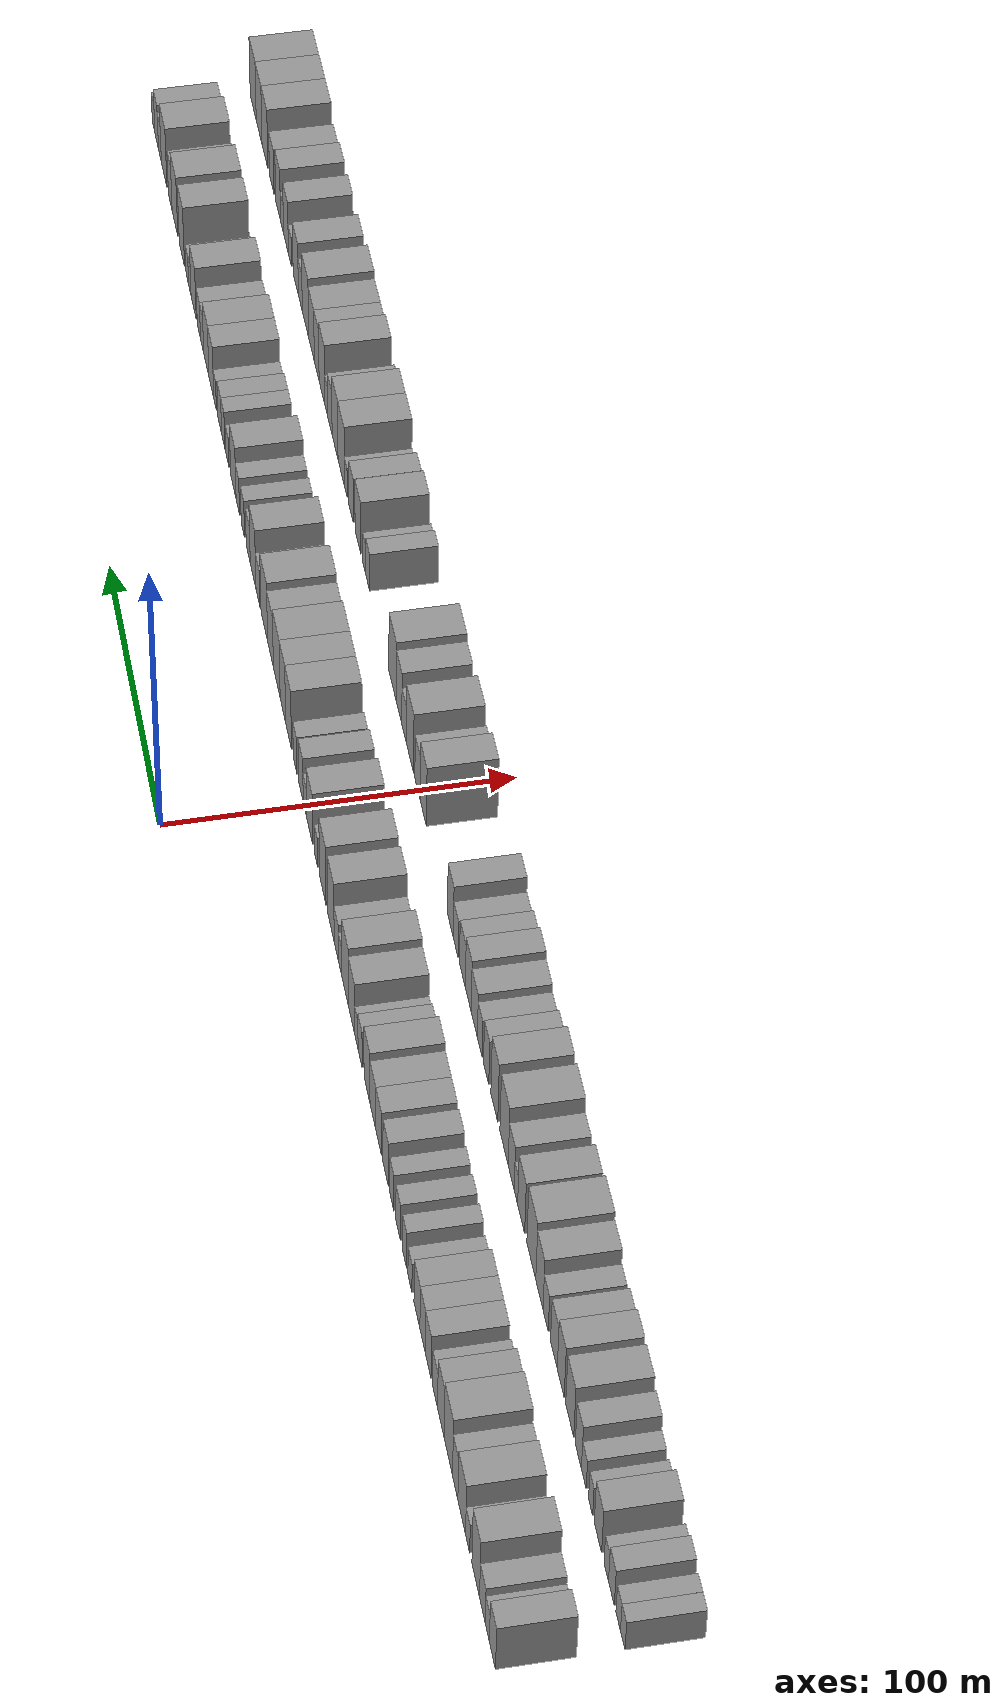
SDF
<sdf version="1.6">
 <world name="default">
  <scene>
   <sky><clouds><speed>12</speed></clouds></sky>
   <ambient>0.4 0.4 0.4 1</ambient>
   <background>0.7 0.7 0.7 1</background>
   <shadows>1</shadows>
  </scene>
  <gravity>0 0 -9.8066</gravity>
  <magnetic_field>6e-06 2.3e-05 -4.2e-05</magnetic_field>
  <physics default="0" name="default_physics" type="ode">
   <ode>
    <solver>
     <type>quick</type>
     <iters>10</iters>
     <sor>1.0</sor>
     <use_dynamic_moi_rescaling>0</use_dynamic_moi_rescaling>
    </solver>
    <constraints>
     <cfm>0</cfm>
     <erp>0.2</erp>
     <contact_max_correcting_vel>100</contact_max_correcting_vel>
     <contact_surface_layer>0.001</contact_surface_layer>
    </constraints>
   </ode>
   <max_step_size>0.004</max_step_size>
   <real_time_factor>1</real_time_factor>
   <real_time_update_rate>250</real_time_update_rate>
  </physics>
  <light name="sun" type="directional">
   <pose>0 0 10 0 0 0</pose>
   <diffuse>0.8 0.8 0.8 1</diffuse>
   <specular>0.2 0.2 0.2 1</specular>
   <attenuation>
    <range>1000</range>
    <constant>0.9</constant>
    <linear>0.01</linear>
    <quadratic>0.001</quadratic>
   </attenuation>
   <direction>-0.5 0.1 -0.9</direction>
  </light>
  <model name="building_1">
   <static>1</static>
   <pose>50.0000 -278.0419 0 0.000000 0.000000 0.000000</pose>
   <link name="link">
    <pose>0 0 9.00 0 0 0</pose>
    <collision name="collision"><geometry><box><size>20.0000 7.9161 18.0000</size></box></geometry></collision>
    <visual name="visual">
     <cast_shadows>0</cast_shadows>
     <geometry><box><size>20.0000 7.9161 18.0000</size></box></geometry>
     <material>
      <script>
       <uri>model://grey_wall/materials/scripts</uri>
       <uri>model://grey_wall/materials/textures</uri>
       <name>vrc/grey_wall</name>
      </script>
     </material>
    </visual>
   </link>
  </model>
  <model name="building_2">
   <static>1</static>
   <pose>50.0000 -271.3548 0 0.000000 0.000000 0.000000</pose>
   <link name="link">
    <pose>0 0 6.00 0 0 0</pose>
    <collision name="collision"><geometry><box><size>20.0000 5.4581 12.0000</size></box></geometry></collision>
    <visual name="visual">
     <cast_shadows>0</cast_shadows>
     <geometry><box><size>20.0000 5.4581 12.0000</size></box></geometry>
     <material>
      <script>
       <uri>model://grey_wall/materials/scripts</uri>
       <uri>model://grey_wall/materials/textures</uri>
       <name>vrc/grey_wall</name>
      </script>
     </material>
    </visual>
   </link>
  </model>
  <model name="building_3">
   <static>1</static>
   <pose>50.0000 -264.9347 0 0.000000 0.000000 0.000000</pose>
   <link name="link">
    <pose>0 0 7.50 0 0 0</pose>
    <collision name="collision"><geometry><box><size>20.0000 7.3822 15.0000</size></box></geometry></collision>
    <visual name="visual">
     <cast_shadows>0</cast_shadows>
     <geometry><box><size>20.0000 7.3822 15.0000</size></box></geometry>
     <material>
      <script>
       <uri>model://grey_wall/materials/scripts</uri>
       <uri>model://grey_wall/materials/textures</uri>
       <name>vrc/grey_wall</name>
      </script>
     </material>
    </visual>
   </link>
  </model>
  <model name="building_4">
   <static>1</static>
   <pose>50.0000 -256.2046 0 0.000000 0.000000 0.000000</pose>
   <link name="link">
    <pose>0 0 12.00 0 0 0</pose>
    <collision name="collision"><geometry><box><size>20.0000 10.0779 24.0000</size></box></geometry></collision>
    <visual name="visual">
     <cast_shadows>0</cast_shadows>
     <geometry><box><size>20.0000 10.0779 24.0000</size></box></geometry>
     <material>
      <script>
       <uri>model://grey_wall/materials/scripts</uri>
       <uri>model://grey_wall/materials/textures</uri>
       <name>vrc/grey_wall</name>
      </script>
     </material>
    </visual>
   </link>
  </model>
  <model name="building_5">
   <static>1</static>
   <pose>50.0000 -245.4248 0 0.000000 0.000000 0.000000</pose>
   <link name="link">
    <pose>0 0 6.00 0 0 0</pose>
    <collision name="collision"><geometry><box><size>20.0000 5.4817 12.0000</size></box></geometry></collision>
    <visual name="visual">
     <cast_shadows>0</cast_shadows>
     <geometry><box><size>20.0000 5.4817 12.0000</size></box></geometry>
     <material>
      <script>
       <uri>model://grey_wall/materials/scripts</uri>
       <uri>model://grey_wall/materials/textures</uri>
       <name>vrc/grey_wall</name>
      </script>
     </material>
    </visual>
   </link>
  </model>
  <model name="building_6">
   <static>1</static>
   <pose>50.0000 -237.4997 0 0.000000 0.000000 0.000000</pose>
   <link name="link">
    <pose>0 0 10.50 0 0 0</pose>
    <collision name="collision"><geometry><box><size>20.0000 10.3685 21.0000</size></box></geometry></collision>
    <visual name="visual">
     <cast_shadows>0</cast_shadows>
     <geometry><box><size>20.0000 10.3685 21.0000</size></box></geometry>
     <material>
      <script>
       <uri>model://grey_wall/materials/scripts</uri>
       <uri>model://grey_wall/materials/textures</uri>
       <name>vrc/grey_wall</name>
      </script>
     </material>
    </visual>
   </link>
  </model>
  <model name="building_7">
   <static>1</static>
   <pose>50.0000 -228.6989 0 0.000000 0.000000 0.000000</pose>
   <link name="link">
    <pose>0 0 9.00 0 0 0</pose>
    <collision name="collision"><geometry><box><size>20.0000 7.2332 18.0000</size></box></geometry></collision>
    <visual name="visual">
     <cast_shadows>0</cast_shadows>
     <geometry><box><size>20.0000 7.2332 18.0000</size></box></geometry>
     <material>
      <script>
       <uri>model://grey_wall/materials/scripts</uri>
       <uri>model://grey_wall/materials/textures</uri>
       <name>vrc/grey_wall</name>
      </script>
     </material>
    </visual>
   </link>
  </model>
  <model name="building_8">
   <static>1</static>
   <pose>50.0000 -219.3549 0 0.000000 0.000000 0.000000</pose>
   <link name="link">
    <pose>0 0 12.00 0 0 0</pose>
    <collision name="collision"><geometry><box><size>20.0000 11.4548 24.0000</size></box></geometry></collision>
    <visual name="visual">
     <cast_shadows>0</cast_shadows>
     <geometry><box><size>20.0000 11.4548 24.0000</size></box></geometry>
     <material>
      <script>
       <uri>model://grey_wall/materials/scripts</uri>
       <uri>model://grey_wall/materials/textures</uri>
       <name>vrc/grey_wall</name>
      </script>
     </material>
    </visual>
   </link>
  </model>
  <model name="building_9">
   <static>1</static>
   <pose>50.0000 -209.0306 0 0.000000 0.000000 0.000000</pose>
   <link name="link">
    <pose>0 0 10.50 0 0 0</pose>
    <collision name="collision"><geometry><box><size>20.0000 9.1938 21.0000</size></box></geometry></collision>
    <visual name="visual">
     <cast_shadows>0</cast_shadows>
     <geometry><box><size>20.0000 9.1938 21.0000</size></box></geometry>
     <material>
      <script>
       <uri>model://grey_wall/materials/scripts</uri>
       <uri>model://grey_wall/materials/textures</uri>
       <name>vrc/grey_wall</name>
      </script>
     </material>
    </visual>
   </link>
  </model>
  <model name="building_10">
   <static>1</static>
   <pose>50.0000 -200.8286 0 0.000000 0.000000 0.000000</pose>
   <link name="link">
    <pose>0 0 7.50 0 0 0</pose>
    <collision name="collision"><geometry><box><size>20.0000 7.2102 15.0000</size></box></geometry></collision>
    <visual name="visual">
     <cast_shadows>0</cast_shadows>
     <geometry><box><size>20.0000 7.2102 15.0000</size></box></geometry>
     <material>
      <script>
       <uri>model://grey_wall/materials/scripts</uri>
       <uri>model://grey_wall/materials/textures</uri>
       <name>vrc/grey_wall</name>
      </script>
     </material>
    </visual>
   </link>
  </model>
  <model name="building_11">
   <static>1</static>
   <pose>50.0000 -191.1680 0 0.000000 0.000000 0.000000</pose>
   <link name="link">
    <pose>0 0 9.00 0 0 0</pose>
    <collision name="collision"><geometry><box><size>20.0000 8.1109 18.0000</size></box></geometry></collision>
    <visual name="visual">
     <cast_shadows>0</cast_shadows>
     <geometry><box><size>20.0000 8.1109 18.0000</size></box></geometry>
     <material>
      <script>
       <uri>model://grey_wall/materials/scripts</uri>
       <uri>model://grey_wall/materials/textures</uri>
       <name>vrc/grey_wall</name>
      </script>
     </material>
    </visual>
   </link>
  </model>
  <model name="building_12">
   <static>1</static>
   <pose>50.0000 -183.3251 0 0.000000 0.000000 0.000000</pose>
   <link name="link">
    <pose>0 0 9.00 0 0 0</pose>
    <collision name="collision"><geometry><box><size>20.0000 7.5751 18.0000</size></box></geometry></collision>
    <visual name="visual">
     <cast_shadows>0</cast_shadows>
     <geometry><box><size>20.0000 7.5751 18.0000</size></box></geometry>
     <material>
      <script>
       <uri>model://grey_wall/materials/scripts</uri>
       <uri>model://grey_wall/materials/textures</uri>
       <name>vrc/grey_wall</name>
      </script>
     </material>
    </visual>
   </link>
  </model>
  <model name="building_13">
   <static>1</static>
   <pose>50.0000 -175.3021 0 0.000000 0.000000 0.000000</pose>
   <link name="link">
    <pose>0 0 9.00 0 0 0</pose>
    <collision name="collision"><geometry><box><size>20.0000 8.4709 18.0000</size></box></geometry></collision>
    <visual name="visual">
     <cast_shadows>0</cast_shadows>
     <geometry><box><size>20.0000 8.4709 18.0000</size></box></geometry>
     <material>
      <script>
       <uri>model://grey_wall/materials/scripts</uri>
       <uri>model://grey_wall/materials/textures</uri>
       <name>vrc/grey_wall</name>
      </script>
     </material>
    </visual>
   </link>
  </model>
  <model name="building_14">
   <static>1</static>
   <pose>50.0000 -165.2082 0 0.000000 0.000000 0.000000</pose>
   <link name="link">
    <pose>0 0 6.00 0 0 0</pose>
    <collision name="collision"><geometry><box><size>20.0000 5.7168 12.0000</size></box></geometry></collision>
    <visual name="visual">
     <cast_shadows>0</cast_shadows>
     <geometry><box><size>20.0000 5.7168 12.0000</size></box></geometry>
     <material>
      <script>
       <uri>model://grey_wall/materials/scripts</uri>
       <uri>model://grey_wall/materials/textures</uri>
       <name>vrc/grey_wall</name>
      </script>
     </material>
    </visual>
   </link>
  </model>
  <model name="building_15">
   <static>1</static>
   <pose>50.0000 -157.3259 0 0.000000 0.000000 0.000000</pose>
   <link name="link">
    <pose>0 0 7.50 0 0 0</pose>
    <collision name="collision"><geometry><box><size>20.0000 6.0478 15.0000</size></box></geometry></collision>
    <visual name="visual">
     <cast_shadows>0</cast_shadows>
     <geometry><box><size>20.0000 6.0478 15.0000</size></box></geometry>
     <material>
      <script>
       <uri>model://grey_wall/materials/scripts</uri>
       <uri>model://grey_wall/materials/textures</uri>
       <name>vrc/grey_wall</name>
      </script>
     </material>
    </visual>
   </link>
  </model>
  <model name="building_16">
   <static>1</static>
   <pose>50.0000 -148.0049 0 0.000000 0.000000 0.000000</pose>
   <link name="link">
    <pose>0 0 7.50 0 0 0</pose>
    <collision name="collision"><geometry><box><size>20.0000 6.5941 15.0000</size></box></geometry></collision>
    <visual name="visual">
     <cast_shadows>0</cast_shadows>
     <geometry><box><size>20.0000 6.5941 15.0000</size></box></geometry>
     <material>
      <script>
       <uri>model://grey_wall/materials/scripts</uri>
       <uri>model://grey_wall/materials/textures</uri>
       <name>vrc/grey_wall</name>
      </script>
     </material>
    </visual>
   </link>
  </model>
  <model name="building_17">
   <static>1</static>
   <pose>50.0000 -138.6632 0 0.000000 0.000000 0.000000</pose>
   <link name="link">
    <pose>0 0 7.50 0 0 0</pose>
    <collision name="collision"><geometry><box><size>20.0000 6.0894 15.0000</size></box></geometry></collision>
    <visual name="visual">
     <cast_shadows>0</cast_shadows>
     <geometry><box><size>20.0000 6.0894 15.0000</size></box></geometry>
     <material>
      <script>
       <uri>model://grey_wall/materials/scripts</uri>
       <uri>model://grey_wall/materials/textures</uri>
       <name>vrc/grey_wall</name>
      </script>
     </material>
    </visual>
   </link>
  </model>
  <model name="building_18">
   <static>1</static>
   <pose>50.0000 -129.5498 0 0.000000 0.000000 0.000000</pose>
   <link name="link">
    <pose>0 0 9.00 0 0 0</pose>
    <collision name="collision"><geometry><box><size>20.0000 8.1373 18.0000</size></box></geometry></collision>
    <visual name="visual">
     <cast_shadows>0</cast_shadows>
     <geometry><box><size>20.0000 8.1373 18.0000</size></box></geometry>
     <material>
      <script>
       <uri>model://grey_wall/materials/scripts</uri>
       <uri>model://grey_wall/materials/textures</uri>
       <name>vrc/grey_wall</name>
      </script>
     </material>
    </visual>
   </link>
  </model>
  <model name="building_19">
   <static>1</static>
   <pose>50.0000 -119.1275 0 0.000000 0.000000 0.000000</pose>
   <link name="link">
    <pose>0 0 9.00 0 0 0</pose>
    <collision name="collision"><geometry><box><size>20.0000 8.7075 18.0000</size></box></geometry></collision>
    <visual name="visual">
     <cast_shadows>0</cast_shadows>
     <geometry><box><size>20.0000 8.7075 18.0000</size></box></geometry>
     <material>
      <script>
       <uri>model://grey_wall/materials/scripts</uri>
       <uri>model://grey_wall/materials/textures</uri>
       <name>vrc/grey_wall</name>
      </script>
     </material>
    </visual>
   </link>
  </model>
  <model name="building_20">
   <static>1</static>
   <pose>50.0000 -110.3166 0 0.000000 0.000000 0.000000</pose>
   <link name="link">
    <pose>0 0 9.00 0 0 0</pose>
    <collision name="collision"><geometry><box><size>20.0000 8.9142 18.0000</size></box></geometry></collision>
    <visual name="visual">
     <cast_shadows>0</cast_shadows>
     <geometry><box><size>20.0000 8.9142 18.0000</size></box></geometry>
     <material>
      <script>
       <uri>model://grey_wall/materials/scripts</uri>
       <uri>model://grey_wall/materials/textures</uri>
       <name>vrc/grey_wall</name>
      </script>
     </material>
    </visual>
   </link>
  </model>
  <model name="building_21">
   <static>1</static>
   <pose>50.0000 -101.2761 0 0.000000 0.000000 0.000000</pose>
   <link name="link">
    <pose>0 0 10.50 0 0 0</pose>
    <collision name="collision"><geometry><box><size>20.0000 9.1668 21.0000</size></box></geometry></collision>
    <visual name="visual">
     <cast_shadows>0</cast_shadows>
     <geometry><box><size>20.0000 9.1668 21.0000</size></box></geometry>
     <material>
      <script>
       <uri>model://grey_wall/materials/scripts</uri>
       <uri>model://grey_wall/materials/textures</uri>
       <name>vrc/grey_wall</name>
      </script>
     </material>
    </visual>
   </link>
  </model>
  <model name="building_22">
   <static>1</static>
   <pose>50.0000 -90.5518 0 0.000000 0.000000 0.000000</pose>
   <link name="link">
    <pose>0 0 7.50 0 0 0</pose>
    <collision name="collision"><geometry><box><size>20.0000 6.2818 15.0000</size></box></geometry></collision>
    <visual name="visual">
     <cast_shadows>0</cast_shadows>
     <geometry><box><size>20.0000 6.2818 15.0000</size></box></geometry>
     <material>
      <script>
       <uri>model://grey_wall/materials/scripts</uri>
       <uri>model://grey_wall/materials/textures</uri>
       <name>vrc/grey_wall</name>
      </script>
     </material>
    </visual>
   </link>
  </model>
  <model name="building_23">
   <static>1</static>
   <pose>50.0000 -84.8986 0 0.000000 0.000000 0.000000</pose>
   <link name="link">
    <pose>0 0 6.00 0 0 0</pose>
    <collision name="collision"><geometry><box><size>20.0000 5.0246 12.0000</size></box></geometry></collision>
    <visual name="visual">
     <cast_shadows>0</cast_shadows>
     <geometry><box><size>20.0000 5.0246 12.0000</size></box></geometry>
     <material>
      <script>
       <uri>model://grey_wall/materials/scripts</uri>
       <uri>model://grey_wall/materials/textures</uri>
       <name>vrc/grey_wall</name>
      </script>
     </material>
    </visual>
   </link>
  </model>
  <model name="building_24">
   <static>1</static>
   <pose>50.0000 -77.4337 0 0.000000 0.000000 0.000000</pose>
   <link name="link">
    <pose>0 0 10.50 0 0 0</pose>
    <collision name="collision"><geometry><box><size>20.0000 9.9053 21.0000</size></box></geometry></collision>
    <visual name="visual">
     <cast_shadows>0</cast_shadows>
     <geometry><box><size>20.0000 9.9053 21.0000</size></box></geometry>
     <material>
      <script>
       <uri>model://grey_wall/materials/scripts</uri>
       <uri>model://grey_wall/materials/textures</uri>
       <name>vrc/grey_wall</name>
      </script>
     </material>
    </visual>
   </link>
  </model>
  <model name="building_25">
   <static>1</static>
   <pose>50.0000 -67.3081 0 0.000000 0.000000 0.000000</pose>
   <link name="link">
    <pose>0 0 12.00 0 0 0</pose>
    <collision name="collision"><geometry><box><size>20.0000 10.3458 24.0000</size></box></geometry></collision>
    <visual name="visual">
     <cast_shadows>0</cast_shadows>
     <geometry><box><size>20.0000 10.3458 24.0000</size></box></geometry>
     <material>
      <script>
       <uri>model://grey_wall/materials/scripts</uri>
       <uri>model://grey_wall/materials/textures</uri>
       <name>vrc/grey_wall</name>
      </script>
     </material>
    </visual>
   </link>
  </model>
  <model name="building_26">
   <static>1</static>
   <pose>50.0000 -59.3123 0 0.000000 0.000000 0.000000</pose>
   <link name="link">
    <pose>0 0 6.00 0 0 0</pose>
    <collision name="collision"><geometry><box><size>20.0000 5.6458 12.0000</size></box></geometry></collision>
    <visual name="visual">
     <cast_shadows>0</cast_shadows>
     <geometry><box><size>20.0000 5.6458 12.0000</size></box></geometry>
     <material>
      <script>
       <uri>model://grey_wall/materials/scripts</uri>
       <uri>model://grey_wall/materials/textures</uri>
       <name>vrc/grey_wall</name>
      </script>
     </material>
    </visual>
   </link>
  </model>
  <model name="building_27">
   <static>1</static>
   <pose>50.0000 -53.0822 0 0.000000 0.000000 0.000000</pose>
   <link name="link">
    <pose>0 0 7.50 0 0 0</pose>
    <collision name="collision"><geometry><box><size>20.0000 6.8145 15.0000</size></box></geometry></collision>
    <visual name="visual">
     <cast_shadows>0</cast_shadows>
     <geometry><box><size>20.0000 6.8145 15.0000</size></box></geometry>
     <material>
      <script>
       <uri>model://grey_wall/materials/scripts</uri>
       <uri>model://grey_wall/materials/textures</uri>
       <name>vrc/grey_wall</name>
      </script>
     </material>
    </visual>
   </link>
  </model>
  <model name="building_28">
   <static>1</static>
   <pose>50.0000 -44.5642 0 0.000000 0.000000 0.000000</pose>
   <link name="link">
    <pose>0 0 12.00 0 0 0</pose>
    <collision name="collision"><geometry><box><size>20.0000 10.2215 24.0000</size></box></geometry></collision>
    <visual name="visual">
     <cast_shadows>0</cast_shadows>
     <geometry><box><size>20.0000 10.2215 24.0000</size></box></geometry>
     <material>
      <script>
       <uri>model://grey_wall/materials/scripts</uri>
       <uri>model://grey_wall/materials/textures</uri>
       <name>vrc/grey_wall</name>
      </script>
     </material>
    </visual>
   </link>
  </model>
  <model name="building_29">
   <static>1</static>
   <pose>50.0000 -31.1216 0 0.000000 0.000000 0.000000</pose>
   <link name="link">
    <pose>0 0 12.00 0 0 0</pose>
    <collision name="collision"><geometry><box><size>20.0000 10.6637 24.0000</size></box></geometry></collision>
    <visual name="visual">
     <cast_shadows>0</cast_shadows>
     <geometry><box><size>20.0000 10.6637 24.0000</size></box></geometry>
     <material>
      <script>
       <uri>model://grey_wall/materials/scripts</uri>
       <uri>model://grey_wall/materials/textures</uri>
       <name>vrc/grey_wall</name>
      </script>
     </material>
    </visual>
   </link>
  </model>
  <model name="building_30">
   <static>1</static>
   <pose>50.0000 -20.1444 0 0.000000 0.000000 0.000000</pose>
   <link name="link">
    <pose>0 0 6.00 0 0 0</pose>
    <collision name="collision"><geometry><box><size>20.0000 5.2907 12.0000</size></box></geometry></collision>
    <visual name="visual">
     <cast_shadows>0</cast_shadows>
     <geometry><box><size>20.0000 5.2907 12.0000</size></box></geometry>
     <material>
      <script>
       <uri>model://grey_wall/materials/scripts</uri>
       <uri>model://grey_wall/materials/textures</uri>
       <name>vrc/grey_wall</name>
      </script>
     </material>
    </visual>
   </link>
  </model>
  <model name="building_31">
   <static>1</static>
   <pose>50.0000 -9.5176 0 0.000000 0.000000 0.000000</pose>
   <link name="link">
    <pose>0 0 10.50 0 0 0</pose>
    <collision name="collision"><geometry><box><size>20.0000 9.9630 21.0000</size></box></geometry></collision>
    <visual name="visual">
     <cast_shadows>0</cast_shadows>
     <geometry><box><size>20.0000 9.9630 21.0000</size></box></geometry>
     <material>
      <script>
       <uri>model://grey_wall/materials/scripts</uri>
       <uri>model://grey_wall/materials/textures</uri>
       <name>vrc/grey_wall</name>
      </script>
     </material>
    </visual>
   </link>
  </model>
  <model name="building_32">
   <static>1</static>
   <pose>50.0000 -1.6180 0 0.000000 0.000000 0.000000</pose>
   <link name="link">
    <pose>0 0 6.00 0 0 0</pose>
    <collision name="collision"><geometry><box><size>20.0000 5.8362 12.0000</size></box></geometry></collision>
    <visual name="visual">
     <cast_shadows>0</cast_shadows>
     <geometry><box><size>20.0000 5.8362 12.0000</size></box></geometry>
     <material>
      <script>
       <uri>model://grey_wall/materials/scripts</uri>
       <uri>model://grey_wall/materials/textures</uri>
       <name>vrc/grey_wall</name>
      </script>
     </material>
    </visual>
   </link>
  </model>
  <model name="building_33">
   <static>1</static>
   <pose>50.0000 5.1053 0 0.000000 0.000000 0.000000</pose>
   <link name="link">
    <pose>0 0 9.00 0 0 0</pose>
    <collision name="collision"><geometry><box><size>20.0000 7.6104 18.0000</size></box></geometry></collision>
    <visual name="visual">
     <cast_shadows>0</cast_shadows>
     <geometry><box><size>20.0000 7.6104 18.0000</size></box></geometry>
     <material>
      <script>
       <uri>model://grey_wall/materials/scripts</uri>
       <uri>model://grey_wall/materials/textures</uri>
       <name>vrc/grey_wall</name>
      </script>
     </material>
    </visual>
   </link>
  </model>
  <model name="building_34">
   <static>1</static>
   <pose>50.0000 15.0317 0 0.000000 0.000000 0.000000</pose>
   <link name="link">
    <pose>0 0 7.50 0 0 0</pose>
    <collision name="collision"><geometry><box><size>20.0000 6.2424 15.0000</size></box></geometry></collision>
    <visual name="visual">
     <cast_shadows>0</cast_shadows>
     <geometry><box><size>20.0000 6.2424 15.0000</size></box></geometry>
     <material>
      <script>
       <uri>model://grey_wall/materials/scripts</uri>
       <uri>model://grey_wall/materials/textures</uri>
       <name>vrc/grey_wall</name>
      </script>
     </material>
    </visual>
   </link>
  </model>
  <model name="building_35">
   <static>1</static>
   <pose>50.0000 26.1771 0 0.000000 0.000000 0.000000</pose>
   <link name="link">
    <pose>0 0 12.00 0 0 0</pose>
    <collision name="collision"><geometry><box><size>20.0000 10.0484 24.0000</size></box></geometry></collision>
    <visual name="visual">
     <cast_shadows>0</cast_shadows>
     <geometry><box><size>20.0000 10.0484 24.0000</size></box></geometry>
     <material>
      <script>
       <uri>model://grey_wall/materials/scripts</uri>
       <uri>model://grey_wall/materials/textures</uri>
       <name>vrc/grey_wall</name>
      </script>
     </material>
    </visual>
   </link>
  </model>
  <model name="building_36">
   <static>1</static>
   <pose>50.0000 36.0595 0 0.000000 0.000000 0.000000</pose>
   <link name="link">
    <pose>0 0 12.00 0 0 0</pose>
    <collision name="collision"><geometry><box><size>20.0000 9.7164 24.0000</size></box></geometry></collision>
    <visual name="visual">
     <cast_shadows>0</cast_shadows>
     <geometry><box><size>20.0000 9.7164 24.0000</size></box></geometry>
     <material>
      <script>
       <uri>model://grey_wall/materials/scripts</uri>
       <uri>model://grey_wall/materials/textures</uri>
       <name>vrc/grey_wall</name>
      </script>
     </material>
    </visual>
   </link>
  </model>
  <model name="building_37">
   <static>1</static>
   <pose>50.0000 46.8024 0 0.000000 0.000000 0.000000</pose>
   <link name="link">
    <pose>0 0 12.00 0 0 0</pose>
    <collision name="collision"><geometry><box><size>20.0000 11.7693 24.0000</size></box></geometry></collision>
    <visual name="visual">
     <cast_shadows>0</cast_shadows>
     <geometry><box><size>20.0000 11.7693 24.0000</size></box></geometry>
     <material>
      <script>
       <uri>model://grey_wall/materials/scripts</uri>
       <uri>model://grey_wall/materials/textures</uri>
       <name>vrc/grey_wall</name>
      </script>
     </material>
    </visual>
   </link>
  </model>
  <model name="building_38">
   <static>1</static>
   <pose>50.0000 57.8174 0 0.000000 0.000000 0.000000</pose>
   <link name="link">
    <pose>0 0 10.50 0 0 0</pose>
    <collision name="collision"><geometry><box><size>20.0000 10.2607 21.0000</size></box></geometry></collision>
    <visual name="visual">
     <cast_shadows>0</cast_shadows>
     <geometry><box><size>20.0000 10.2607 21.0000</size></box></geometry>
     <material>
      <script>
       <uri>model://grey_wall/materials/scripts</uri>
       <uri>model://grey_wall/materials/textures</uri>
       <name>vrc/grey_wall</name>
      </script>
     </material>
    </visual>
   </link>
  </model>
  <model name="building_39">
   <static>1</static>
   <pose>50.0000 68.8495 0 0.000000 0.000000 0.000000</pose>
   <link name="link">
    <pose>0 0 12.00 0 0 0</pose>
    <collision name="collision"><geometry><box><size>20.0000 11.8035 24.0000</size></box></geometry></collision>
    <visual name="visual">
     <cast_shadows>0</cast_shadows>
     <geometry><box><size>20.0000 11.8035 24.0000</size></box></geometry>
     <material>
      <script>
       <uri>model://grey_wall/materials/scripts</uri>
       <uri>model://grey_wall/materials/textures</uri>
       <name>vrc/grey_wall</name>
      </script>
     </material>
    </visual>
   </link>
  </model>
  <model name="building_40">
   <static>1</static>
   <pose>50.0000 80.2737 0 0.000000 0.000000 0.000000</pose>
   <link name="link">
    <pose>0 0 7.50 0 0 0</pose>
    <collision name="collision"><geometry><box><size>20.0000 7.0448 15.0000</size></box></geometry></collision>
    <visual name="visual">
     <cast_shadows>0</cast_shadows>
     <geometry><box><size>20.0000 7.0448 15.0000</size></box></geometry>
     <material>
      <script>
       <uri>model://grey_wall/materials/scripts</uri>
       <uri>model://grey_wall/materials/textures</uri>
       <name>vrc/grey_wall</name>
      </script>
     </material>
    </visual>
   </link>
  </model>
  <model name="building_41">
   <static>1</static>
   <pose>50.0000 89.0135 0 0.000000 0.000000 0.000000</pose>
   <link name="link">
    <pose>0 0 12.00 0 0 0</pose>
    <collision name="collision"><geometry><box><size>20.0000 10.4349 24.0000</size></box></geometry></collision>
    <visual name="visual">
     <cast_shadows>0</cast_shadows>
     <geometry><box><size>20.0000 10.4349 24.0000</size></box></geometry>
     <material>
      <script>
       <uri>model://grey_wall/materials/scripts</uri>
       <uri>model://grey_wall/materials/textures</uri>
       <name>vrc/grey_wall</name>
      </script>
     </material>
    </visual>
   </link>
  </model>
  <model name="building_42">
   <static>1</static>
   <pose>50.0000 97.9409 0 0.000000 0.000000 0.000000</pose>
   <link name="link">
    <pose>0 0 7.50 0 0 0</pose>
    <collision name="collision"><geometry><box><size>20.0000 7.4198 15.0000</size></box></geometry></collision>
    <visual name="visual">
     <cast_shadows>0</cast_shadows>
     <geometry><box><size>20.0000 7.4198 15.0000</size></box></geometry>
     <material>
      <script>
       <uri>model://grey_wall/materials/scripts</uri>
       <uri>model://grey_wall/materials/textures</uri>
       <name>vrc/grey_wall</name>
      </script>
     </material>
    </visual>
   </link>
  </model>
  <model name="building_43">
   <static>1</static>
   <pose>50.0000 107.7863 0 0.000000 0.000000 0.000000</pose>
   <link name="link">
    <pose>0 0 7.50 0 0 0</pose>
    <collision name="collision"><geometry><box><size>20.0000 6.2710 15.0000</size></box></geometry></collision>
    <visual name="visual">
     <cast_shadows>0</cast_shadows>
     <geometry><box><size>20.0000 6.2710 15.0000</size></box></geometry>
     <material>
      <script>
       <uri>model://grey_wall/materials/scripts</uri>
       <uri>model://grey_wall/materials/textures</uri>
       <name>vrc/grey_wall</name>
      </script>
     </material>
    </visual>
   </link>
  </model>
  <model name="building_44">
   <static>1</static>
   <pose>50.0000 117.1740 0 0.000000 0.000000 0.000000</pose>
   <link name="link">
    <pose>0 0 7.50 0 0 0</pose>
    <collision name="collision"><geometry><box><size>20.0000 6.5045 15.0000</size></box></geometry></collision>
    <visual name="visual">
     <cast_shadows>0</cast_shadows>
     <geometry><box><size>20.0000 6.5045 15.0000</size></box></geometry>
     <material>
      <script>
       <uri>model://grey_wall/materials/scripts</uri>
       <uri>model://grey_wall/materials/textures</uri>
       <name>vrc/grey_wall</name>
      </script>
     </material>
    </visual>
   </link>
  </model>
  <model name="building_45">
   <static>1</static>
   <pose>50.0000 125.5380 0 0.000000 0.000000 0.000000</pose>
   <link name="link">
    <pose>0 0 10.50 0 0 0</pose>
    <collision name="collision"><geometry><box><size>20.0000 10.2234 21.0000</size></box></geometry></collision>
    <visual name="visual">
     <cast_shadows>0</cast_shadows>
     <geometry><box><size>20.0000 10.2234 21.0000</size></box></geometry>
     <material>
      <script>
       <uri>model://grey_wall/materials/scripts</uri>
       <uri>model://grey_wall/materials/textures</uri>
       <name>vrc/grey_wall</name>
      </script>
     </material>
    </visual>
   </link>
  </model>
  <model name="building_46">
   <static>1</static>
   <pose>50.0000 136.6007 0 0.000000 0.000000 0.000000</pose>
   <link name="link">
    <pose>0 0 6.00 0 0 0</pose>
    <collision name="collision"><geometry><box><size>20.0000 5.9021 12.0000</size></box></geometry></collision>
    <visual name="visual">
     <cast_shadows>0</cast_shadows>
     <geometry><box><size>20.0000 5.9021 12.0000</size></box></geometry>
     <material>
      <script>
       <uri>model://grey_wall/materials/scripts</uri>
       <uri>model://grey_wall/materials/textures</uri>
       <name>vrc/grey_wall</name>
      </script>
     </material>
    </visual>
   </link>
  </model>
  <model name="building_47">
   <static>1</static>
   <pose>50.0000 144.6621 0 0.000000 0.000000 0.000000</pose>
   <link name="link">
    <pose>0 0 7.50 0 0 0</pose>
    <collision name="collision"><geometry><box><size>20.0000 6.2205 15.0000</size></box></geometry></collision>
    <visual name="visual">
     <cast_shadows>0</cast_shadows>
     <geometry><box><size>20.0000 6.2205 15.0000</size></box></geometry>
     <material>
      <script>
       <uri>model://grey_wall/materials/scripts</uri>
       <uri>model://grey_wall/materials/textures</uri>
       <name>vrc/grey_wall</name>
      </script>
     </material>
    </visual>
   </link>
  </model>
  <model name="building_48">
   <static>1</static>
   <pose>50.0000 151.2966 0 0.000000 0.000000 0.000000</pose>
   <link name="link">
    <pose>0 0 7.50 0 0 0</pose>
    <collision name="collision"><geometry><box><size>20.0000 7.0485 15.0000</size></box></geometry></collision>
    <visual name="visual">
     <cast_shadows>0</cast_shadows>
     <geometry><box><size>20.0000 7.0485 15.0000</size></box></geometry>
     <material>
      <script>
       <uri>model://grey_wall/materials/scripts</uri>
       <uri>model://grey_wall/materials/textures</uri>
       <name>vrc/grey_wall</name>
      </script>
     </material>
    </visual>
   </link>
  </model>
  <model name="building_49">
   <static>1</static>
   <pose>50.0000 160.3709 0 0.000000 0.000000 0.000000</pose>
   <link name="link">
    <pose>0 0 6.00 0 0 0</pose>
    <collision name="collision"><geometry><box><size>20.0000 5.1000 12.0000</size></box></geometry></collision>
    <visual name="visual">
     <cast_shadows>0</cast_shadows>
     <geometry><box><size>20.0000 5.1000 12.0000</size></box></geometry>
     <material>
      <script>
       <uri>model://grey_wall/materials/scripts</uri>
       <uri>model://grey_wall/materials/textures</uri>
       <name>vrc/grey_wall</name>
      </script>
     </material>
    </visual>
   </link>
  </model>
  <model name="building_50">
   <static>1</static>
   <pose>50.0000 167.5924 0 0.000000 0.000000 0.000000</pose>
   <link name="link">
    <pose>0 0 10.50 0 0 0</pose>
    <collision name="collision"><geometry><box><size>20.0000 9.3429 21.0000</size></box></geometry></collision>
    <visual name="visual">
     <cast_shadows>0</cast_shadows>
     <geometry><box><size>20.0000 9.3429 21.0000</size></box></geometry>
     <material>
      <script>
       <uri>model://grey_wall/materials/scripts</uri>
       <uri>model://grey_wall/materials/textures</uri>
       <name>vrc/grey_wall</name>
      </script>
     </material>
    </visual>
   </link>
  </model>
  <model name="building_51">
   <static>1</static>
   <pose>50.0000 177.4050 0 0.000000 0.000000 0.000000</pose>
   <link name="link">
    <pose>0 0 10.50 0 0 0</pose>
    <collision name="collision"><geometry><box><size>20.0000 10.2823 21.0000</size></box></geometry></collision>
    <visual name="visual">
     <cast_shadows>0</cast_shadows>
     <geometry><box><size>20.0000 10.2823 21.0000</size></box></geometry>
     <material>
      <script>
       <uri>model://grey_wall/materials/scripts</uri>
       <uri>model://grey_wall/materials/textures</uri>
       <name>vrc/grey_wall</name>
      </script>
     </material>
    </visual>
   </link>
  </model>
  <model name="building_52">
   <static>1</static>
   <pose>50.0000 185.6972 0 0.000000 0.000000 0.000000</pose>
   <link name="link">
    <pose>0 0 7.50 0 0 0</pose>
    <collision name="collision"><geometry><box><size>20.0000 6.3021 15.0000</size></box></geometry></collision>
    <visual name="visual">
     <cast_shadows>0</cast_shadows>
     <geometry><box><size>20.0000 6.3021 15.0000</size></box></geometry>
     <material>
      <script>
       <uri>model://grey_wall/materials/scripts</uri>
       <uri>model://grey_wall/materials/textures</uri>
       <name>vrc/grey_wall</name>
      </script>
     </material>
    </visual>
   </link>
  </model>
  <model name="building_53">
   <static>1</static>
   <pose>50.0000 192.0240 0 0.000000 0.000000 0.000000</pose>
   <link name="link">
    <pose>0 0 7.50 0 0 0</pose>
    <collision name="collision"><geometry><box><size>20.0000 6.3515 15.0000</size></box></geometry></collision>
    <visual name="visual">
     <cast_shadows>0</cast_shadows>
     <geometry><box><size>20.0000 6.3515 15.0000</size></box></geometry>
     <material>
      <script>
       <uri>model://grey_wall/materials/scripts</uri>
       <uri>model://grey_wall/materials/textures</uri>
       <name>vrc/grey_wall</name>
      </script>
     </material>
    </visual>
   </link>
  </model>
  <model name="building_54">
   <static>1</static>
   <pose>50.0000 202.4204 0 0.000000 0.000000 0.000000</pose>
   <link name="link">
    <pose>0 0 10.50 0 0 0</pose>
    <collision name="collision"><geometry><box><size>20.0000 10.4414 21.0000</size></box></geometry></collision>
    <visual name="visual">
     <cast_shadows>0</cast_shadows>
     <geometry><box><size>20.0000 10.4414 21.0000</size></box></geometry>
     <material>
      <script>
       <uri>model://grey_wall/materials/scripts</uri>
       <uri>model://grey_wall/materials/textures</uri>
       <name>vrc/grey_wall</name>
      </script>
     </material>
    </visual>
   </link>
  </model>
  <model name="building_55">
   <static>1</static>
   <pose>50.0000 210.0939 0 0.000000 0.000000 0.000000</pose>
   <link name="link">
    <pose>0 0 6.00 0 0 0</pose>
    <collision name="collision"><geometry><box><size>20.0000 4.9056 12.0000</size></box></geometry></collision>
    <visual name="visual">
     <cast_shadows>0</cast_shadows>
     <geometry><box><size>20.0000 4.9056 12.0000</size></box></geometry>
     <material>
      <script>
       <uri>model://grey_wall/materials/scripts</uri>
       <uri>model://grey_wall/materials/textures</uri>
       <name>vrc/grey_wall</name>
      </script>
     </material>
    </visual>
   </link>
  </model>
  <model name="building_56">
   <static>1</static>
   <pose>50.0000 215.1791 0 0.000000 0.000000 0.000000</pose>
   <link name="link">
    <pose>0 0 6.00 0 0 0</pose>
    <collision name="collision"><geometry><box><size>20.0000 5.2647 12.0000</size></box></geometry></collision>
    <visual name="visual">
     <cast_shadows>0</cast_shadows>
     <geometry><box><size>20.0000 5.2647 12.0000</size></box></geometry>
     <material>
      <script>
       <uri>model://grey_wall/materials/scripts</uri>
       <uri>model://grey_wall/materials/textures</uri>
       <name>vrc/grey_wall</name>
      </script>
     </material>
    </visual>
   </link>
  </model>
  <model name="building_57">
   <static>1</static>
   <pose>50.0000 226.1138 0 0.000000 0.000000 0.000000</pose>
   <link name="link">
    <pose>0 0 12.00 0 0 0</pose>
    <collision name="collision"><geometry><box><size>20.0000 10.6047 24.0000</size></box></geometry></collision>
    <visual name="visual">
     <cast_shadows>0</cast_shadows>
     <geometry><box><size>20.0000 10.6047 24.0000</size></box></geometry>
     <material>
      <script>
       <uri>model://grey_wall/materials/scripts</uri>
       <uri>model://grey_wall/materials/textures</uri>
       <name>vrc/grey_wall</name>
      </script>
     </material>
    </visual>
   </link>
  </model>
  <model name="building_58">
   <static>1</static>
   <pose>50.0000 240.3249 0 0.000000 0.000000 0.000000</pose>
   <link name="link">
    <pose>0 0 12.00 0 0 0</pose>
    <collision name="collision"><geometry><box><size>20.0000 11.8175 24.0000</size></box></geometry></collision>
    <visual name="visual">
     <cast_shadows>0</cast_shadows>
     <geometry><box><size>20.0000 11.8175 24.0000</size></box></geometry>
     <material>
      <script>
       <uri>model://grey_wall/materials/scripts</uri>
       <uri>model://grey_wall/materials/textures</uri>
       <name>vrc/grey_wall</name>
      </script>
     </material>
    </visual>
   </link>
  </model>
  <model name="building_59">
   <static>1</static>
   <pose>50.0000 250.0452 0 0.000000 0.000000 0.000000</pose>
   <link name="link">
    <pose>0 0 9.00 0 0 0</pose>
    <collision name="collision"><geometry><box><size>20.0000 7.6230 18.0000</size></box></geometry></collision>
    <visual name="visual">
     <cast_shadows>0</cast_shadows>
     <geometry><box><size>20.0000 7.6230 18.0000</size></box></geometry>
     <material>
      <script>
       <uri>model://grey_wall/materials/scripts</uri>
       <uri>model://grey_wall/materials/textures</uri>
       <name>vrc/grey_wall</name>
      </script>
     </material>
    </visual>
   </link>
  </model>
  <model name="building_60">
   <static>1</static>
   <pose>50.0000 262.7953 0 0.000000 0.000000 0.000000</pose>
   <link name="link">
    <pose>0 0 12.00 0 0 0</pose>
    <collision name="collision"><geometry><box><size>20.0000 11.8773 24.0000</size></box></geometry></collision>
    <visual name="visual">
     <cast_shadows>0</cast_shadows>
     <geometry><box><size>20.0000 11.8773 24.0000</size></box></geometry>
     <material>
      <script>
       <uri>model://grey_wall/materials/scripts</uri>
       <uri>model://grey_wall/materials/textures</uri>
       <name>vrc/grey_wall</name>
      </script>
     </material>
    </visual>
   </link>
  </model>
  <model name="building_61">
   <static>1</static>
   <pose>50.0000 271.7701 0 0.000000 0.000000 0.000000</pose>
   <link name="link">
    <pose>0 0 7.50 0 0 0</pose>
    <collision name="collision"><geometry><box><size>20.0000 6.0723 15.0000</size></box></geometry></collision>
    <visual name="visual">
     <cast_shadows>0</cast_shadows>
     <geometry><box><size>20.0000 6.0723 15.0000</size></box></geometry>
     <material>
      <script>
       <uri>model://grey_wall/materials/scripts</uri>
       <uri>model://grey_wall/materials/textures</uri>
       <name>vrc/grey_wall</name>
      </script>
     </material>
    </visual>
   </link>
  </model>
  <model name="building_62">
   <static>1</static>
   <pose>50.0000 278.5875 0 0.000000 0.000000 0.000000</pose>
   <link name="link">
    <pose>0 0 9.00 0 0 0</pose>
    <collision name="collision"><geometry><box><size>20.0000 7.5625 18.0000</size></box></geometry></collision>
    <visual name="visual">
     <cast_shadows>0</cast_shadows>
     <geometry><box><size>20.0000 7.5625 18.0000</size></box></geometry>
     <material>
      <script>
       <uri>model://grey_wall/materials/scripts</uri>
       <uri>model://grey_wall/materials/textures</uri>
       <name>vrc/grey_wall</name>
      </script>
     </material>
    </visual>
   </link>
  </model>
  <model name="building_63">
   <static>1</static>
   <pose>50.0000 285.1560 0 0.000000 0.000000 0.000000</pose>
   <link name="link">
    <pose>0 0 6.00 0 0 0</pose>
    <collision name="collision"><geometry><box><size>20.0000 5.5745 12.0000</size></box></geometry></collision>
    <visual name="visual">
     <cast_shadows>0</cast_shadows>
     <geometry><box><size>20.0000 5.5745 12.0000</size></box></geometry>
     <material>
      <script>
       <uri>model://grey_wall/materials/scripts</uri>
       <uri>model://grey_wall/materials/textures</uri>
       <name>vrc/grey_wall</name>
      </script>
     </material>
    </visual>
   </link>
  </model>
  <model name="building_64">
   <static>1</static>
   <pose>82.0000 -279.3072 0 0.000000 0.000000 0.000000</pose>
   <link name="link">
    <pose>0 0 6.00 0 0 0</pose>
    <collision name="collision"><geometry><box><size>20.0000 5.3857 12.0000</size></box></geometry></collision>
    <visual name="visual">
     <cast_shadows>0</cast_shadows>
     <geometry><box><size>20.0000 5.3857 12.0000</size></box></geometry>
     <material>
      <script>
       <uri>model://grey_wall/materials/scripts</uri>
       <uri>model://grey_wall/materials/textures</uri>
       <name>vrc/grey_wall</name>
      </script>
     </material>
    </visual>
   </link>
  </model>
  <model name="building_65">
   <static>1</static>
   <pose>82.0000 -273.8731 0 0.000000 0.000000 0.000000</pose>
   <link name="link">
    <pose>0 0 6.00 0 0 0</pose>
    <collision name="collision"><geometry><box><size>20.0000 5.4824 12.0000</size></box></geometry></collision>
    <visual name="visual">
     <cast_shadows>0</cast_shadows>
     <geometry><box><size>20.0000 5.4824 12.0000</size></box></geometry>
     <material>
      <script>
       <uri>model://grey_wall/materials/scripts</uri>
       <uri>model://grey_wall/materials/textures</uri>
       <name>vrc/grey_wall</name>
      </script>
     </material>
    </visual>
   </link>
  </model>
  <model name="building_66">
   <static>1</static>
   <pose>82.0000 -265.6224 0 0.000000 0.000000 0.000000</pose>
   <link name="link">
    <pose>0 0 7.50 0 0 0</pose>
    <collision name="collision"><geometry><box><size>20.0000 7.0191 15.0000</size></box></geometry></collision>
    <visual name="visual">
     <cast_shadows>0</cast_shadows>
     <geometry><box><size>20.0000 7.0191 15.0000</size></box></geometry>
     <material>
      <script>
       <uri>model://grey_wall/materials/scripts</uri>
       <uri>model://grey_wall/materials/textures</uri>
       <name>vrc/grey_wall</name>
      </script>
     </material>
    </visual>
   </link>
  </model>
  <model name="building_67">
   <static>1</static>
   <pose>82.0000 -259.4065 0 0.000000 0.000000 0.000000</pose>
   <link name="link">
    <pose>0 0 6.00 0 0 0</pose>
    <collision name="collision"><geometry><box><size>20.0000 5.4126 12.0000</size></box></geometry></collision>
    <visual name="visual">
     <cast_shadows>0</cast_shadows>
     <geometry><box><size>20.0000 5.4126 12.0000</size></box></geometry>
     <material>
      <script>
       <uri>model://grey_wall/materials/scripts</uri>
       <uri>model://grey_wall/materials/textures</uri>
       <name>vrc/grey_wall</name>
      </script>
     </material>
    </visual>
   </link>
  </model>
  <model name="building_68">
   <static>1</static>
   <pose>82.0000 -249.2070 0 0.000000 0.000000 0.000000</pose>
   <link name="link">
    <pose>0 0 9.00 0 0 0</pose>
    <collision name="collision"><geometry><box><size>20.0000 8.9863 18.0000</size></box></geometry></collision>
    <visual name="visual">
     <cast_shadows>0</cast_shadows>
     <geometry><box><size>20.0000 8.9863 18.0000</size></box></geometry>
     <material>
      <script>
       <uri>model://grey_wall/materials/scripts</uri>
       <uri>model://grey_wall/materials/textures</uri>
       <name>vrc/grey_wall</name>
      </script>
     </material>
    </visual>
   </link>
  </model>
  <model name="building_69">
   <static>1</static>
   <pose>82.0000 -240.1617 0 0.000000 0.000000 0.000000</pose>
   <link name="link">
    <pose>0 0 6.00 0 0 0</pose>
    <collision name="collision"><geometry><box><size>20.0000 5.1044 12.0000</size></box></geometry></collision>
    <visual name="visual">
     <cast_shadows>0</cast_shadows>
     <geometry><box><size>20.0000 5.1044 12.0000</size></box></geometry>
     <material>
      <script>
       <uri>model://grey_wall/materials/scripts</uri>
       <uri>model://grey_wall/materials/textures</uri>
       <name>vrc/grey_wall</name>
      </script>
     </material>
    </visual>
   </link>
  </model>
  <model name="building_70">
   <static>1</static>
   <pose>82.0000 -231.6276 0 0.000000 0.000000 0.000000</pose>
   <link name="link">
    <pose>0 0 6.00 0 0 0</pose>
    <collision name="collision"><geometry><box><size>20.0000 5.9638 12.0000</size></box></geometry></collision>
    <visual name="visual">
     <cast_shadows>0</cast_shadows>
     <geometry><box><size>20.0000 5.9638 12.0000</size></box></geometry>
     <material>
      <script>
       <uri>model://grey_wall/materials/scripts</uri>
       <uri>model://grey_wall/materials/textures</uri>
       <name>vrc/grey_wall</name>
      </script>
     </material>
    </visual>
   </link>
  </model>
  <model name="building_71">
   <static>1</static>
   <pose>82.0000 -224.7965 0 0.000000 0.000000 0.000000</pose>
   <link name="link">
    <pose>0 0 9.00 0 0 0</pose>
    <collision name="collision"><geometry><box><size>20.0000 7.6984 18.0000</size></box></geometry></collision>
    <visual name="visual">
     <cast_shadows>0</cast_shadows>
     <geometry><box><size>20.0000 7.6984 18.0000</size></box></geometry>
     <material>
      <script>
       <uri>model://grey_wall/materials/scripts</uri>
       <uri>model://grey_wall/materials/textures</uri>
       <name>vrc/grey_wall</name>
      </script>
     </material>
    </visual>
   </link>
  </model>
  <model name="building_72">
   <static>1</static>
   <pose>82.0000 -213.8456 0 0.000000 0.000000 0.000000</pose>
   <link name="link">
    <pose>0 0 10.50 0 0 0</pose>
    <collision name="collision"><geometry><box><size>20.0000 10.2033 21.0000</size></box></geometry></collision>
    <visual name="visual">
     <cast_shadows>0</cast_shadows>
     <geometry><box><size>20.0000 10.2033 21.0000</size></box></geometry>
     <material>
      <script>
       <uri>model://grey_wall/materials/scripts</uri>
       <uri>model://grey_wall/materials/textures</uri>
       <name>vrc/grey_wall</name>
      </script>
     </material>
    </visual>
   </link>
  </model>
  <model name="building_73">
   <static>1</static>
   <pose>82.0000 -202.2812 0 0.000000 0.000000 0.000000</pose>
   <link name="link">
    <pose>0 0 10.50 0 0 0</pose>
    <collision name="collision"><geometry><box><size>20.0000 8.9257 21.0000</size></box></geometry></collision>
    <visual name="visual">
     <cast_shadows>0</cast_shadows>
     <geometry><box><size>20.0000 8.9257 21.0000</size></box></geometry>
     <material>
      <script>
       <uri>model://grey_wall/materials/scripts</uri>
       <uri>model://grey_wall/materials/textures</uri>
       <name>vrc/grey_wall</name>
      </script>
     </material>
    </visual>
   </link>
  </model>
  <model name="building_74">
   <static>1</static>
   <pose>82.0000 -193.4574 0 0.000000 0.000000 0.000000</pose>
   <link name="link">
    <pose>0 0 9.00 0 0 0</pose>
    <collision name="collision"><geometry><box><size>20.0000 8.7218 18.0000</size></box></geometry></collision>
    <visual name="visual">
     <cast_shadows>0</cast_shadows>
     <geometry><box><size>20.0000 8.7218 18.0000</size></box></geometry>
     <material>
      <script>
       <uri>model://grey_wall/materials/scripts</uri>
       <uri>model://grey_wall/materials/textures</uri>
       <name>vrc/grey_wall</name>
      </script>
     </material>
    </visual>
   </link>
  </model>
  <model name="building_75">
   <static>1</static>
   <pose>82.0000 -182.6572 0 0.000000 0.000000 0.000000</pose>
   <link name="link">
    <pose>0 0 7.50 0 0 0</pose>
    <collision name="collision"><geometry><box><size>20.0000 6.8787 15.0000</size></box></geometry></collision>
    <visual name="visual">
     <cast_shadows>0</cast_shadows>
     <geometry><box><size>20.0000 6.8787 15.0000</size></box></geometry>
     <material>
      <script>
       <uri>model://grey_wall/materials/scripts</uri>
       <uri>model://grey_wall/materials/textures</uri>
       <name>vrc/grey_wall</name>
      </script>
     </material>
    </visual>
   </link>
  </model>
  <model name="building_76">
   <static>1</static>
   <pose>82.0000 -174.4313 0 0.000000 0.000000 0.000000</pose>
   <link name="link">
    <pose>0 0 10.50 0 0 0</pose>
    <collision name="collision"><geometry><box><size>20.0000 9.5731 21.0000</size></box></geometry></collision>
    <visual name="visual">
     <cast_shadows>0</cast_shadows>
     <geometry><box><size>20.0000 9.5731 21.0000</size></box></geometry>
     <material>
      <script>
       <uri>model://grey_wall/materials/scripts</uri>
       <uri>model://grey_wall/materials/textures</uri>
       <name>vrc/grey_wall</name>
      </script>
     </material>
    </visual>
   </link>
  </model>
  <model name="building_77">
   <static>1</static>
   <pose>82.0000 -163.6680 0 0.000000 0.000000 0.000000</pose>
   <link name="link">
    <pose>0 0 12.00 0 0 0</pose>
    <collision name="collision"><geometry><box><size>20.0000 11.9535 24.0000</size></box></geometry></collision>
    <visual name="visual">
     <cast_shadows>0</cast_shadows>
     <geometry><box><size>20.0000 11.9535 24.0000</size></box></geometry>
     <material>
      <script>
       <uri>model://grey_wall/materials/scripts</uri>
       <uri>model://grey_wall/materials/textures</uri>
       <name>vrc/grey_wall</name>
      </script>
     </material>
    </visual>
   </link>
  </model>
  <model name="building_78">
   <static>1</static>
   <pose>82.0000 -149.9595 0 0.000000 0.000000 0.000000</pose>
   <link name="link">
    <pose>0 0 10.50 0 0 0</pose>
    <collision name="collision"><geometry><box><size>20.0000 9.4634 21.0000</size></box></geometry></collision>
    <visual name="visual">
     <cast_shadows>0</cast_shadows>
     <geometry><box><size>20.0000 9.4634 21.0000</size></box></geometry>
     <material>
      <script>
       <uri>model://grey_wall/materials/scripts</uri>
       <uri>model://grey_wall/materials/textures</uri>
       <name>vrc/grey_wall</name>
      </script>
     </material>
    </visual>
   </link>
  </model>
  <model name="building_79">
   <static>1</static>
   <pose>82.0000 -142.8215 0 0.000000 0.000000 0.000000</pose>
   <link name="link">
    <pose>0 0 6.00 0 0 0</pose>
    <collision name="collision"><geometry><box><size>20.0000 4.8126 12.0000</size></box></geometry></collision>
    <visual name="visual">
     <cast_shadows>0</cast_shadows>
     <geometry><box><size>20.0000 4.8126 12.0000</size></box></geometry>
     <material>
      <script>
       <uri>model://grey_wall/materials/scripts</uri>
       <uri>model://grey_wall/materials/textures</uri>
       <name>vrc/grey_wall</name>
      </script>
     </material>
    </visual>
   </link>
  </model>
  <model name="building_80">
   <static>1</static>
   <pose>82.0000 -136.3421 0 0.000000 0.000000 0.000000</pose>
   <link name="link">
    <pose>0 0 9.00 0 0 0</pose>
    <collision name="collision"><geometry><box><size>20.0000 8.1463 18.0000</size></box></geometry></collision>
    <visual name="visual">
     <cast_shadows>0</cast_shadows>
     <geometry><box><size>20.0000 8.1463 18.0000</size></box></geometry>
     <material>
      <script>
       <uri>model://grey_wall/materials/scripts</uri>
       <uri>model://grey_wall/materials/textures</uri>
       <name>vrc/grey_wall</name>
      </script>
     </material>
    </visual>
   </link>
  </model>
  <model name="building_81">
   <static>1</static>
   <pose>82.0000 -126.5177 0 0.000000 0.000000 0.000000</pose>
   <link name="link">
    <pose>0 0 12.00 0 0 0</pose>
    <collision name="collision"><geometry><box><size>20.0000 11.5023 24.0000</size></box></geometry></collision>
    <visual name="visual">
     <cast_shadows>0</cast_shadows>
     <geometry><box><size>20.0000 11.5023 24.0000</size></box></geometry>
     <material>
      <script>
       <uri>model://grey_wall/materials/scripts</uri>
       <uri>model://grey_wall/materials/textures</uri>
       <name>vrc/grey_wall</name>
      </script>
     </material>
    </visual>
   </link>
  </model>
  <model name="building_82">
   <static>1</static>
   <pose>82.0000 -112.9433 0 0.000000 0.000000 0.000000</pose>
   <link name="link">
    <pose>0 0 12.00 0 0 0</pose>
    <collision name="collision"><geometry><box><size>20.0000 9.6467 24.0000</size></box></geometry></collision>
    <visual name="visual">
     <cast_shadows>0</cast_shadows>
     <geometry><box><size>20.0000 9.6467 24.0000</size></box></geometry>
     <material>
      <script>
       <uri>model://grey_wall/materials/scripts</uri>
       <uri>model://grey_wall/materials/textures</uri>
       <name>vrc/grey_wall</name>
      </script>
     </material>
    </visual>
   </link>
  </model>
  <model name="building_83">
   <static>1</static>
   <pose>82.0000 -101.4091 0 0.000000 0.000000 0.000000</pose>
   <link name="link">
    <pose>0 0 9.00 0 0 0</pose>
    <collision name="collision"><geometry><box><size>20.0000 7.4216 18.0000</size></box></geometry></collision>
    <visual name="visual">
     <cast_shadows>0</cast_shadows>
     <geometry><box><size>20.0000 7.4216 18.0000</size></box></geometry>
     <material>
      <script>
       <uri>model://grey_wall/materials/scripts</uri>
       <uri>model://grey_wall/materials/textures</uri>
       <name>vrc/grey_wall</name>
      </script>
     </material>
    </visual>
   </link>
  </model>
  <model name="building_84">
   <static>1</static>
   <pose>82.0000 -92.3058 0 0.000000 0.000000 0.000000</pose>
   <link name="link">
    <pose>0 0 7.50 0 0 0</pose>
    <collision name="collision"><geometry><box><size>20.0000 6.7851 15.0000</size></box></geometry></collision>
    <visual name="visual">
     <cast_shadows>0</cast_shadows>
     <geometry><box><size>20.0000 6.7851 15.0000</size></box></geometry>
     <material>
      <script>
       <uri>model://grey_wall/materials/scripts</uri>
       <uri>model://grey_wall/materials/textures</uri>
       <name>vrc/grey_wall</name>
      </script>
     </material>
    </visual>
   </link>
  </model>
  <model name="building_85">
   <static>1</static>
   <pose>82.0000 -84.4193 0 0.000000 0.000000 0.000000</pose>
   <link name="link">
    <pose>0 0 9.00 0 0 0</pose>
    <collision name="collision"><geometry><box><size>20.0000 8.9878 18.0000</size></box></geometry></collision>
    <visual name="visual">
     <cast_shadows>0</cast_shadows>
     <geometry><box><size>20.0000 8.9878 18.0000</size></box></geometry>
     <material>
      <script>
       <uri>model://grey_wall/materials/scripts</uri>
       <uri>model://grey_wall/materials/textures</uri>
       <name>vrc/grey_wall</name>
      </script>
     </material>
    </visual>
   </link>
  </model>
  <model name="building_86">
   <static>1</static>
   <pose>82.0000 -75.6813 0 0.000000 0.000000 0.000000</pose>
   <link name="link">
    <pose>0 0 10.50 0 0 0</pose>
    <collision name="collision"><geometry><box><size>20.0000 8.4882 21.0000</size></box></geometry></collision>
    <visual name="visual">
     <cast_shadows>0</cast_shadows>
     <geometry><box><size>20.0000 8.4882 21.0000</size></box></geometry>
     <material>
      <script>
       <uri>model://grey_wall/materials/scripts</uri>
       <uri>model://grey_wall/materials/textures</uri>
       <name>vrc/grey_wall</name>
      </script>
     </material>
    </visual>
   </link>
  </model>
  <model name="building_87">
   <static>1</static>
   <pose>82.0000 -67.1716 0 0.000000 0.000000 0.000000</pose>
   <link name="link">
    <pose>0 0 9.00 0 0 0</pose>
    <collision name="collision"><geometry><box><size>20.0000 8.5313 18.0000</size></box></geometry></collision>
    <visual name="visual">
     <cast_shadows>0</cast_shadows>
     <geometry><box><size>20.0000 8.5313 18.0000</size></box></geometry>
     <material>
      <script>
       <uri>model://grey_wall/materials/scripts</uri>
       <uri>model://grey_wall/materials/textures</uri>
       <name>vrc/grey_wall</name>
      </script>
     </material>
    </visual>
   </link>
  </model>
  <model name="building_88">
   <static>1</static>
   <pose>82.0000 -57.3082 0 0.000000 0.000000 0.000000</pose>
   <link name="link">
    <pose>0 0 7.50 0 0 0</pose>
    <collision name="collision"><geometry><box><size>20.0000 7.1954 15.0000</size></box></geometry></collision>
    <visual name="visual">
     <cast_shadows>0</cast_shadows>
     <geometry><box><size>20.0000 7.1954 15.0000</size></box></geometry>
     <material>
      <script>
       <uri>model://grey_wall/materials/scripts</uri>
       <uri>model://grey_wall/materials/textures</uri>
       <name>vrc/grey_wall</name>
      </script>
     </material>
    </visual>
   </link>
  </model>
  <model name="building_89">
   <static>1</static>
   <pose>82.0000 -49.3834 0 0.000000 0.000000 0.000000</pose>
   <link name="link">
    <pose>0 0 10.50 0 0 0</pose>
    <collision name="collision"><geometry><box><size>20.0000 8.6541 21.0000</size></box></geometry></collision>
    <visual name="visual">
     <cast_shadows>0</cast_shadows>
     <geometry><box><size>20.0000 8.6541 21.0000</size></box></geometry>
     <material>
      <script>
       <uri>model://grey_wall/materials/scripts</uri>
       <uri>model://grey_wall/materials/textures</uri>
       <name>vrc/grey_wall</name>
      </script>
     </material>
    </visual>
   </link>
  </model>
  <model name="building_90">
   <static>1</static>
   <pose>82.0000 -8.3676 0 0.000000 0.000000 0.000000</pose>
   <link name="link">
    <pose>0 0 12.00 0 0 0</pose>
    <collision name="collision"><geometry><box><size>20.0000 9.7925 24.0000</size></box></geometry></collision>
    <visual name="visual">
     <cast_shadows>0</cast_shadows>
     <geometry><box><size>20.0000 9.7925 24.0000</size></box></geometry>
     <material>
      <script>
       <uri>model://grey_wall/materials/scripts</uri>
       <uri>model://grey_wall/materials/textures</uri>
       <name>vrc/grey_wall</name>
      </script>
     </material>
    </visual>
   </link>
  </model>
  <model name="building_91">
   <static>1</static>
   <pose>82.0000 0.6084 0 0.000000 0.000000 0.000000</pose>
   <link name="link">
    <pose>0 0 9.00 0 0 0</pose>
    <collision name="collision"><geometry><box><size>20.0000 8.1593 18.0000</size></box></geometry></collision>
    <visual name="visual">
     <cast_shadows>0</cast_shadows>
     <geometry><box><size>20.0000 8.1593 18.0000</size></box></geometry>
     <material>
      <script>
       <uri>model://grey_wall/materials/scripts</uri>
       <uri>model://grey_wall/materials/textures</uri>
       <name>vrc/grey_wall</name>
      </script>
     </material>
    </visual>
   </link>
  </model>
  <model name="building_92">
   <static>1</static>
   <pose>82.0000 12.4325 0 0.000000 0.000000 0.000000</pose>
   <link name="link">
    <pose>0 0 12.00 0 0 0</pose>
    <collision name="collision"><geometry><box><size>20.0000 11.4890 24.0000</size></box></geometry></collision>
    <visual name="visual">
     <cast_shadows>0</cast_shadows>
     <geometry><box><size>20.0000 11.4890 24.0000</size></box></geometry>
     <material>
      <script>
       <uri>model://grey_wall/materials/scripts</uri>
       <uri>model://grey_wall/materials/textures</uri>
       <name>vrc/grey_wall</name>
      </script>
     </material>
    </visual>
   </link>
  </model>
  <model name="building_93">
   <static>1</static>
   <pose>82.0000 21.6987 0 0.000000 0.000000 0.000000</pose>
   <link name="link">
    <pose>0 0 7.50 0 0 0</pose>
    <collision name="collision"><geometry><box><size>20.0000 7.0435 15.0000</size></box></geometry></collision>
    <visual name="visual">
     <cast_shadows>0</cast_shadows>
     <geometry><box><size>20.0000 7.0435 15.0000</size></box></geometry>
     <material>
      <script>
       <uri>model://grey_wall/materials/scripts</uri>
       <uri>model://grey_wall/materials/textures</uri>
       <name>vrc/grey_wall</name>
      </script>
     </material>
    </visual>
   </link>
  </model>
  <model name="building_94">
   <static>1</static>
   <pose>82.0000 29.6810 0 0.000000 0.000000 0.000000</pose>
   <link name="link">
    <pose>0 0 10.50 0 0 0</pose>
    <collision name="collision"><geometry><box><size>20.0000 8.9211 21.0000</size></box></geometry></collision>
    <visual name="visual">
     <cast_shadows>0</cast_shadows>
     <geometry><box><size>20.0000 8.9211 21.0000</size></box></geometry>
     <material>
      <script>
       <uri>model://grey_wall/materials/scripts</uri>
       <uri>model://grey_wall/materials/textures</uri>
       <name>vrc/grey_wall</name>
      </script>
     </material>
    </visual>
   </link>
  </model>
  <model name="building_95">
   <static>1</static>
   <pose>82.0000 40.0631 0 0.000000 0.000000 0.000000</pose>
   <link name="link">
    <pose>0 0 12.00 0 0 0</pose>
    <collision name="collision"><geometry><box><size>20.0000 11.8431 24.0000</size></box></geometry></collision>
    <visual name="visual">
     <cast_shadows>0</cast_shadows>
     <geometry><box><size>20.0000 11.8431 24.0000</size></box></geometry>
     <material>
      <script>
       <uri>model://grey_wall/materials/scripts</uri>
       <uri>model://grey_wall/materials/textures</uri>
       <name>vrc/grey_wall</name>
      </script>
     </material>
    </visual>
   </link>
  </model>
  <model name="building_96">
   <static>1</static>
   <pose>82.0000 80.6784 0 0.000000 0.000000 0.000000</pose>
   <link name="link">
    <pose>0 0 7.50 0 0 0</pose>
    <collision name="collision"><geometry><box><size>20.0000 6.4625 15.0000</size></box></geometry></collision>
    <visual name="visual">
     <cast_shadows>0</cast_shadows>
     <geometry><box><size>20.0000 6.4625 15.0000</size></box></geometry>
     <material>
      <script>
       <uri>model://grey_wall/materials/scripts</uri>
       <uri>model://grey_wall/materials/textures</uri>
       <name>vrc/grey_wall</name>
      </script>
     </material>
    </visual>
   </link>
  </model>
  <model name="building_97">
   <static>1</static>
   <pose>82.0000 86.6667 0 0.000000 0.000000 0.000000</pose>
   <link name="link">
    <pose>0 0 6.00 0 0 0</pose>
    <collision name="collision"><geometry><box><size>20.0000 5.5141 12.0000</size></box></geometry></collision>
    <visual name="visual">
     <cast_shadows>0</cast_shadows>
     <geometry><box><size>20.0000 5.5141 12.0000</size></box></geometry>
     <material>
      <script>
       <uri>model://grey_wall/materials/scripts</uri>
       <uri>model://grey_wall/materials/textures</uri>
       <name>vrc/grey_wall</name>
      </script>
     </material>
    </visual>
   </link>
  </model>
  <model name="building_98">
   <static>1</static>
   <pose>82.0000 97.2709 0 0.000000 0.000000 0.000000</pose>
   <link name="link">
    <pose>0 0 10.50 0 0 0</pose>
    <collision name="collision"><geometry><box><size>20.0000 9.6942 21.0000</size></box></geometry></collision>
    <visual name="visual">
     <cast_shadows>0</cast_shadows>
     <geometry><box><size>20.0000 9.6942 21.0000</size></box></geometry>
     <material>
      <script>
       <uri>model://grey_wall/materials/scripts</uri>
       <uri>model://grey_wall/materials/textures</uri>
       <name>vrc/grey_wall</name>
      </script>
     </material>
    </visual>
   </link>
  </model>
  <model name="building_99">
   <static>1</static>
   <pose>82.0000 108.8838 0 0.000000 0.000000 0.000000</pose>
   <link name="link">
    <pose>0 0 9.00 0 0 0</pose>
    <collision name="collision"><geometry><box><size>20.0000 7.5317 18.0000</size></box></geometry></collision>
    <visual name="visual">
     <cast_shadows>0</cast_shadows>
     <geometry><box><size>20.0000 7.5317 18.0000</size></box></geometry>
     <material>
      <script>
       <uri>model://grey_wall/materials/scripts</uri>
       <uri>model://grey_wall/materials/textures</uri>
       <name>vrc/grey_wall</name>
      </script>
     </material>
    </visual>
   </link>
  </model>
  <model name="building_100">
   <static>1</static>
   <pose>82.0000 118.0510 0 0.000000 0.000000 0.000000</pose>
   <link name="link">
    <pose>0 0 6.00 0 0 0</pose>
    <collision name="collision"><geometry><box><size>20.0000 4.8027 12.0000</size></box></geometry></collision>
    <visual name="visual">
     <cast_shadows>0</cast_shadows>
     <geometry><box><size>20.0000 4.8027 12.0000</size></box></geometry>
     <material>
      <script>
       <uri>model://grey_wall/materials/scripts</uri>
       <uri>model://grey_wall/materials/textures</uri>
       <name>vrc/grey_wall</name>
      </script>
     </material>
    </visual>
   </link>
  </model>
  <model name="building_101">
   <static>1</static>
   <pose>82.0000 125.9457 0 0.000000 0.000000 0.000000</pose>
   <link name="link">
    <pose>0 0 12.00 0 0 0</pose>
    <collision name="collision"><geometry><box><size>20.0000 10.9868 24.0000</size></box></geometry></collision>
    <visual name="visual">
     <cast_shadows>0</cast_shadows>
     <geometry><box><size>20.0000 10.9868 24.0000</size></box></geometry>
     <material>
      <script>
       <uri>model://grey_wall/materials/scripts</uri>
       <uri>model://grey_wall/materials/textures</uri>
       <name>vrc/grey_wall</name>
      </script>
     </material>
    </visual>
   </link>
  </model>
  <model name="building_102">
   <static>1</static>
   <pose>82.0000 136.6268 0 0.000000 0.000000 0.000000</pose>
   <link name="link">
    <pose>0 0 12.00 0 0 0</pose>
    <collision name="collision"><geometry><box><size>20.0000 10.3753 24.0000</size></box></geometry></collision>
    <visual name="visual">
     <cast_shadows>0</cast_shadows>
     <geometry><box><size>20.0000 10.3753 24.0000</size></box></geometry>
     <material>
      <script>
       <uri>model://grey_wall/materials/scripts</uri>
       <uri>model://grey_wall/materials/textures</uri>
       <name>vrc/grey_wall</name>
      </script>
     </material>
    </visual>
   </link>
  </model>
  <model name="building_103">
   <static>1</static>
   <pose>82.0000 145.6771 0 0.000000 0.000000 0.000000</pose>
   <link name="link">
    <pose>0 0 9.00 0 0 0</pose>
    <collision name="collision"><geometry><box><size>20.0000 7.7253 18.0000</size></box></geometry></collision>
    <visual name="visual">
     <cast_shadows>0</cast_shadows>
     <geometry><box><size>20.0000 7.7253 18.0000</size></box></geometry>
     <material>
      <script>
       <uri>model://grey_wall/materials/scripts</uri>
       <uri>model://grey_wall/materials/textures</uri>
       <name>vrc/grey_wall</name>
      </script>
     </material>
    </visual>
   </link>
  </model>
  <model name="building_104">
   <static>1</static>
   <pose>82.0000 152.2177 0 0.000000 0.000000 0.000000</pose>
   <link name="link">
    <pose>0 0 6.00 0 0 0</pose>
    <collision name="collision"><geometry><box><size>20.0000 5.3559 12.0000</size></box></geometry></collision>
    <visual name="visual">
     <cast_shadows>0</cast_shadows>
     <geometry><box><size>20.0000 5.3559 12.0000</size></box></geometry>
     <material>
      <script>
       <uri>model://grey_wall/materials/scripts</uri>
       <uri>model://grey_wall/materials/textures</uri>
       <name>vrc/grey_wall</name>
      </script>
     </material>
    </visual>
   </link>
  </model>
  <model name="building_105">
   <static>1</static>
   <pose>82.0000 159.8796 0 0.000000 0.000000 0.000000</pose>
   <link name="link">
    <pose>0 0 12.00 0 0 0</pose>
    <collision name="collision"><geometry><box><size>20.0000 9.9680 24.0000</size></box></geometry></collision>
    <visual name="visual">
     <cast_shadows>0</cast_shadows>
     <geometry><box><size>20.0000 9.9680 24.0000</size></box></geometry>
     <material>
      <script>
       <uri>model://grey_wall/materials/scripts</uri>
       <uri>model://grey_wall/materials/textures</uri>
       <name>vrc/grey_wall</name>
      </script>
     </material>
    </visual>
   </link>
  </model>
  <model name="building_106">
   <static>1</static>
   <pose>82.0000 169.1822 0 0.000000 0.000000 0.000000</pose>
   <link name="link">
    <pose>0 0 10.50 0 0 0</pose>
    <collision name="collision"><geometry><box><size>20.0000 8.6370 21.0000</size></box></geometry></collision>
    <visual name="visual">
     <cast_shadows>0</cast_shadows>
     <geometry><box><size>20.0000 8.6370 21.0000</size></box></geometry>
     <material>
      <script>
       <uri>model://grey_wall/materials/scripts</uri>
       <uri>model://grey_wall/materials/textures</uri>
       <name>vrc/grey_wall</name>
      </script>
     </material>
    </visual>
   </link>
  </model>
  <model name="building_107">
   <static>1</static>
   <pose>82.0000 178.6078 0 0.000000 0.000000 0.000000</pose>
   <link name="link">
    <pose>0 0 10.50 0 0 0</pose>
    <collision name="collision"><geometry><box><size>20.0000 10.2143 21.0000</size></box></geometry></collision>
    <visual name="visual">
     <cast_shadows>0</cast_shadows>
     <geometry><box><size>20.0000 10.2143 21.0000</size></box></geometry>
     <material>
      <script>
       <uri>model://grey_wall/materials/scripts</uri>
       <uri>model://grey_wall/materials/textures</uri>
       <name>vrc/grey_wall</name>
      </script>
     </material>
    </visual>
   </link>
  </model>
  <model name="building_108">
   <static>1</static>
   <pose>82.0000 189.5355 0 0.000000 0.000000 0.000000</pose>
   <link name="link">
    <pose>0 0 12.00 0 0 0</pose>
    <collision name="collision"><geometry><box><size>20.0000 11.6410 24.0000</size></box></geometry></collision>
    <visual name="visual">
     <cast_shadows>0</cast_shadows>
     <geometry><box><size>20.0000 11.6410 24.0000</size></box></geometry>
     <material>
      <script>
       <uri>model://grey_wall/materials/scripts</uri>
       <uri>model://grey_wall/materials/textures</uri>
       <name>vrc/grey_wall</name>
      </script>
     </material>
    </visual>
   </link>
  </model>
  <model name="building_109">
   <static>1</static>
   <pose>82.0000 198.9463 0 0.000000 0.000000 0.000000</pose>
   <link name="link">
    <pose>0 0 7.50 0 0 0</pose>
    <collision name="collision"><geometry><box><size>20.0000 7.1807 15.0000</size></box></geometry></collision>
    <visual name="visual">
     <cast_shadows>0</cast_shadows>
     <geometry><box><size>20.0000 7.1807 15.0000</size></box></geometry>
     <material>
      <script>
       <uri>model://grey_wall/materials/scripts</uri>
       <uri>model://grey_wall/materials/textures</uri>
       <name>vrc/grey_wall</name>
      </script>
     </material>
    </visual>
   </link>
  </model>
  <model name="building_110">
   <static>1</static>
   <pose>82.0000 207.3932 0 0.000000 0.000000 0.000000</pose>
   <link name="link">
    <pose>0 0 10.50 0 0 0</pose>
    <collision name="collision"><geometry><box><size>20.0000 9.7129 21.0000</size></box></geometry></collision>
    <visual name="visual">
     <cast_shadows>0</cast_shadows>
     <geometry><box><size>20.0000 9.7129 21.0000</size></box></geometry>
     <material>
      <script>
       <uri>model://grey_wall/materials/scripts</uri>
       <uri>model://grey_wall/materials/textures</uri>
       <name>vrc/grey_wall</name>
      </script>
     </material>
    </visual>
   </link>
  </model>
  <model name="building_111">
   <static>1</static>
   <pose>82.0000 218.1797 0 0.000000 0.000000 0.000000</pose>
   <link name="link">
    <pose>0 0 6.00 0 0 0</pose>
    <collision name="collision"><geometry><box><size>20.0000 5.8603 12.0000</size></box></geometry></collision>
    <visual name="visual">
     <cast_shadows>0</cast_shadows>
     <geometry><box><size>20.0000 5.8603 12.0000</size></box></geometry>
     <material>
      <script>
       <uri>model://grey_wall/materials/scripts</uri>
       <uri>model://grey_wall/materials/textures</uri>
       <name>vrc/grey_wall</name>
      </script>
     </material>
    </visual>
   </link>
  </model>
  <model name="building_112">
   <static>1</static>
   <pose>82.0000 225.6800 0 0.000000 0.000000 0.000000</pose>
   <link name="link">
    <pose>0 0 10.50 0 0 0</pose>
    <collision name="collision"><geometry><box><size>20.0000 9.1404 21.0000</size></box></geometry></collision>
    <visual name="visual">
     <cast_shadows>0</cast_shadows>
     <geometry><box><size>20.0000 9.1404 21.0000</size></box></geometry>
     <material>
      <script>
       <uri>model://grey_wall/materials/scripts</uri>
       <uri>model://grey_wall/materials/textures</uri>
       <name>vrc/grey_wall</name>
      </script>
     </material>
    </visual>
   </link>
  </model>
  <model name="building_113">
   <static>1</static>
   <pose>82.0000 233.0842 0 0.000000 0.000000 0.000000</pose>
   <link name="link">
    <pose>0 0 6.00 0 0 0</pose>
    <collision name="collision"><geometry><box><size>20.0000 5.6680 12.0000</size></box></geometry></collision>
    <visual name="visual">
     <cast_shadows>0</cast_shadows>
     <geometry><box><size>20.0000 5.6680 12.0000</size></box></geometry>
     <material>
      <script>
       <uri>model://grey_wall/materials/scripts</uri>
       <uri>model://grey_wall/materials/textures</uri>
       <name>vrc/grey_wall</name>
      </script>
     </material>
    </visual>
   </link>
  </model>
  <model name="building_114">
   <static>1</static>
   <pose>82.0000 240.5529 0 0.000000 0.000000 0.000000</pose>
   <link name="link">
    <pose>0 0 10.50 0 0 0</pose>
    <collision name="collision"><geometry><box><size>20.0000 9.2693 21.0000</size></box></geometry></collision>
    <visual name="visual">
     <cast_shadows>0</cast_shadows>
     <geometry><box><size>20.0000 9.2693 21.0000</size></box></geometry>
     <material>
      <script>
       <uri>model://grey_wall/materials/scripts</uri>
       <uri>model://grey_wall/materials/textures</uri>
       <name>vrc/grey_wall</name>
      </script>
     </material>
    </visual>
   </link>
  </model>
  <model name="building_115">
   <static>1</static>
   <pose>82.0000 252.6492 0 0.000000 0.000000 0.000000</pose>
   <link name="link">
    <pose>0 0 9.00 0 0 0</pose>
    <collision name="collision"><geometry><box><size>20.0000 8.9233 18.0000</size></box></geometry></collision>
    <visual name="visual">
     <cast_shadows>0</cast_shadows>
     <geometry><box><size>20.0000 8.9233 18.0000</size></box></geometry>
     <material>
      <script>
       <uri>model://grey_wall/materials/scripts</uri>
       <uri>model://grey_wall/materials/textures</uri>
       <name>vrc/grey_wall</name>
      </script>
     </material>
    </visual>
   </link>
  </model>
  <model name="building_116">
   <static>1</static>
   <pose>82.0000 265.8233 0 0.000000 0.000000 0.000000</pose>
   <link name="link">
    <pose>0 0 12.00 0 0 0</pose>
    <collision name="collision"><geometry><box><size>20.0000 11.4250 24.0000</size></box></geometry></collision>
    <visual name="visual">
     <cast_shadows>0</cast_shadows>
     <geometry><box><size>20.0000 11.4250 24.0000</size></box></geometry>
     <material>
      <script>
       <uri>model://grey_wall/materials/scripts</uri>
       <uri>model://grey_wall/materials/textures</uri>
       <name>vrc/grey_wall</name>
      </script>
     </material>
    </visual>
   </link>
  </model>
  <model name="building_117">
   <static>1</static>
   <pose>82.0000 277.2405 0 0.000000 0.000000 0.000000</pose>
   <link name="link">
    <pose>0 0 12.00 0 0 0</pose>
    <collision name="collision"><geometry><box><size>20.0000 11.4095 24.0000</size></box></geometry></collision>
    <visual name="visual">
     <cast_shadows>0</cast_shadows>
     <geometry><box><size>20.0000 11.4095 24.0000</size></box></geometry>
     <material>
      <script>
       <uri>model://grey_wall/materials/scripts</uri>
       <uri>model://grey_wall/materials/textures</uri>
       <name>vrc/grey_wall</name>
      </script>
     </material>
    </visual>
   </link>
  </model>
  <model name="building_118">
   <static>1</static>
   <pose>82.0000 288.8339 0 0.000000 0.000000 0.000000</pose>
   <link name="link">
    <pose>0 0 12.00 0 0 0</pose>
    <collision name="collision"><geometry><box><size>20.0000 11.7773 24.0000</size></box></geometry></collision>
    <visual name="visual">
     <cast_shadows>0</cast_shadows>
     <geometry><box><size>20.0000 11.7773 24.0000</size></box></geometry>
     <material>
      <script>
       <uri>model://grey_wall/materials/scripts</uri>
       <uri>model://grey_wall/materials/textures</uri>
       <name>vrc/grey_wall</name>
      </script>
     </material>
    </visual>
   </link>
  </model>
 </world>
</sdf>
